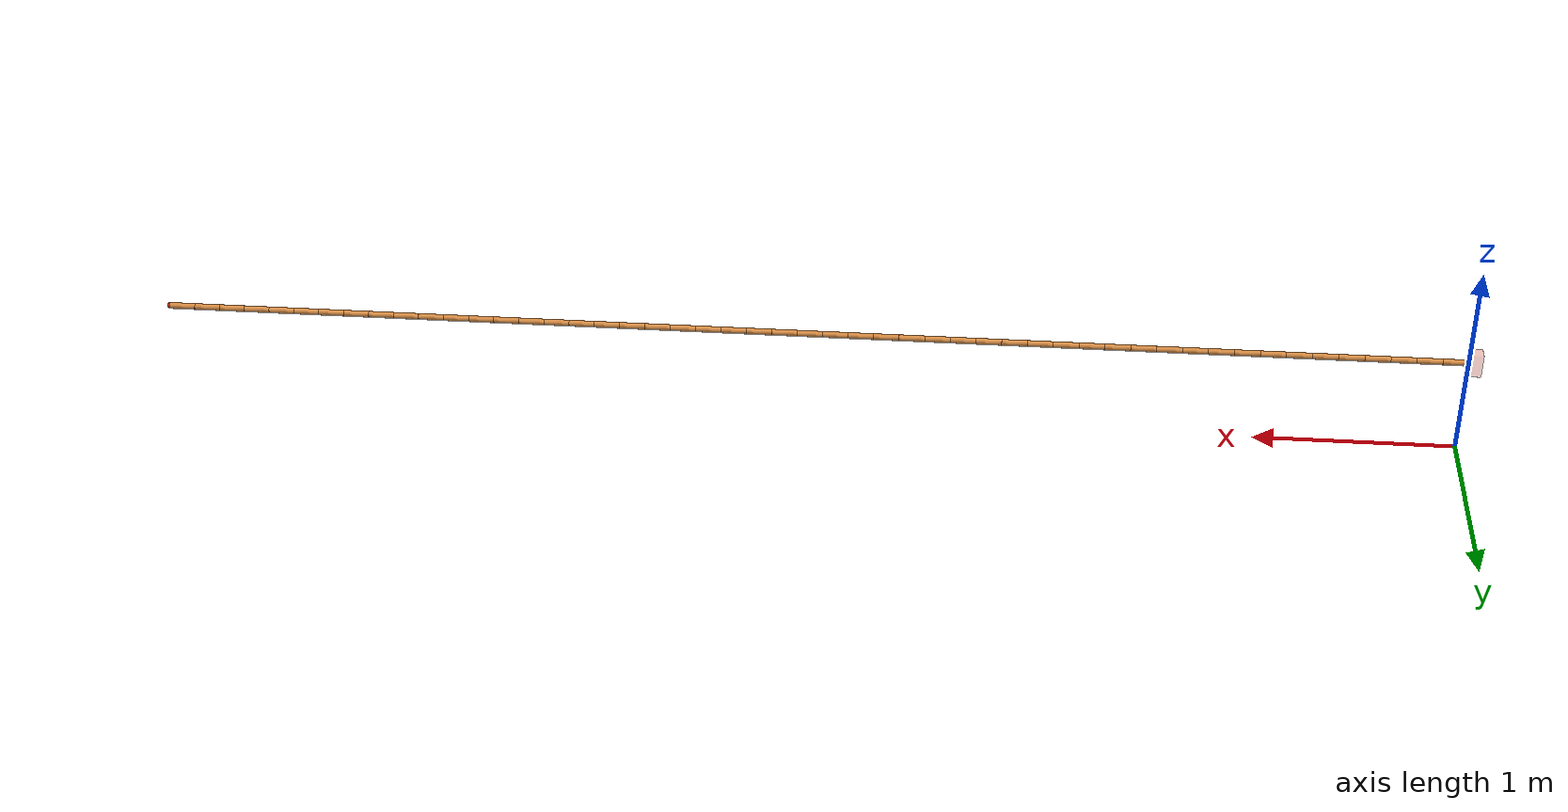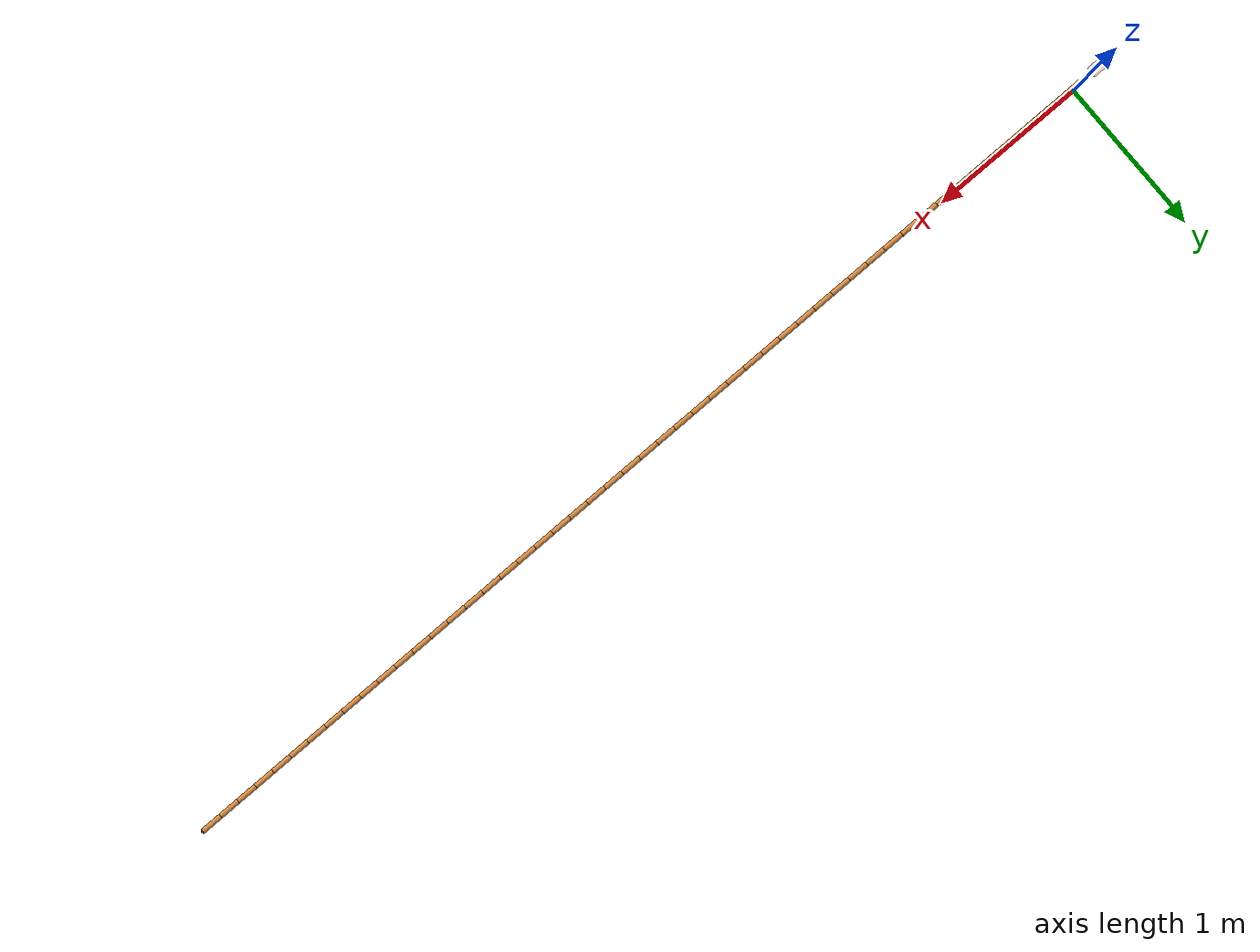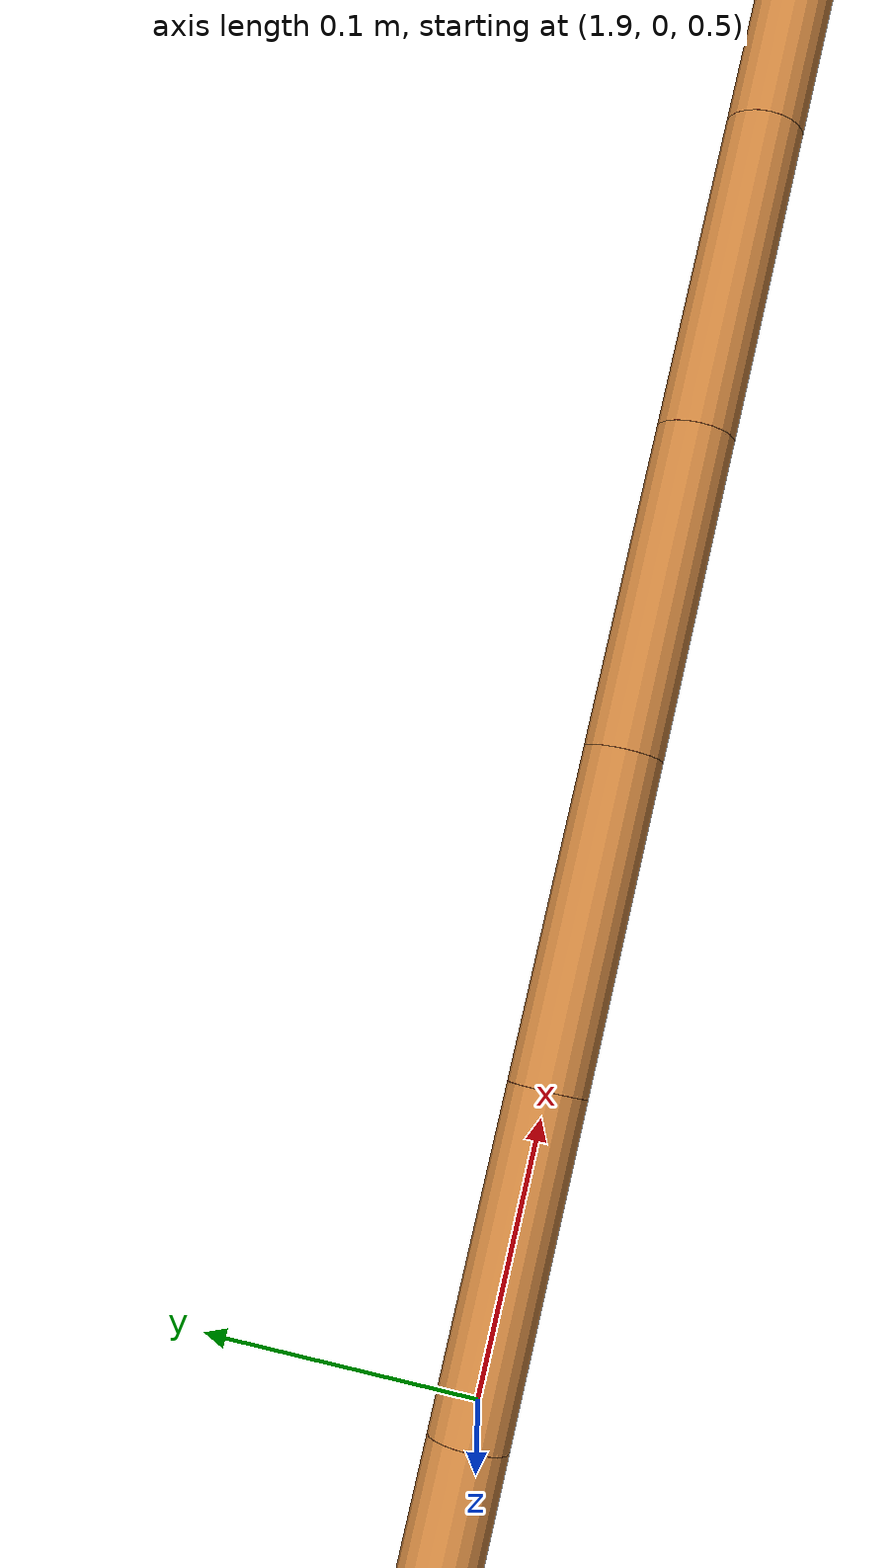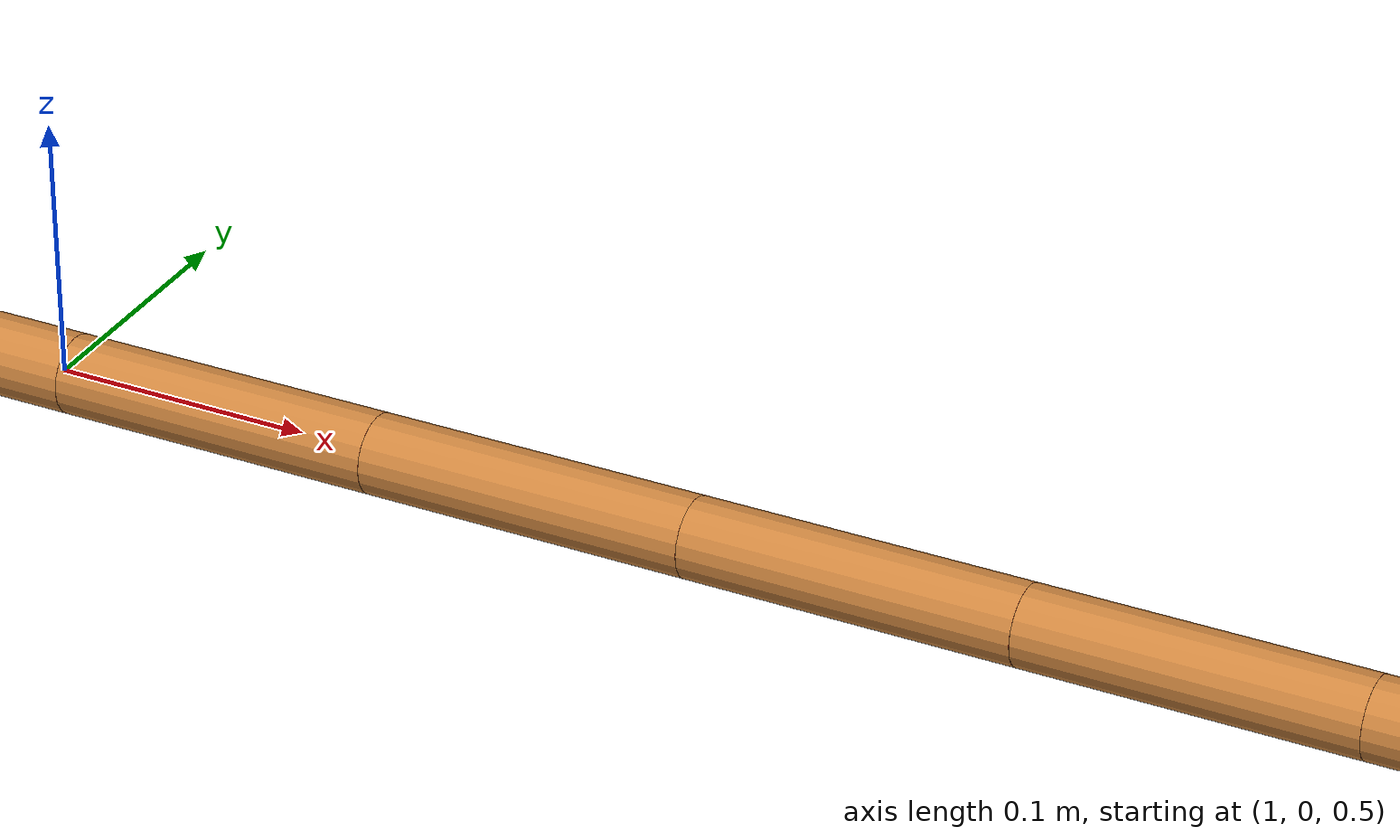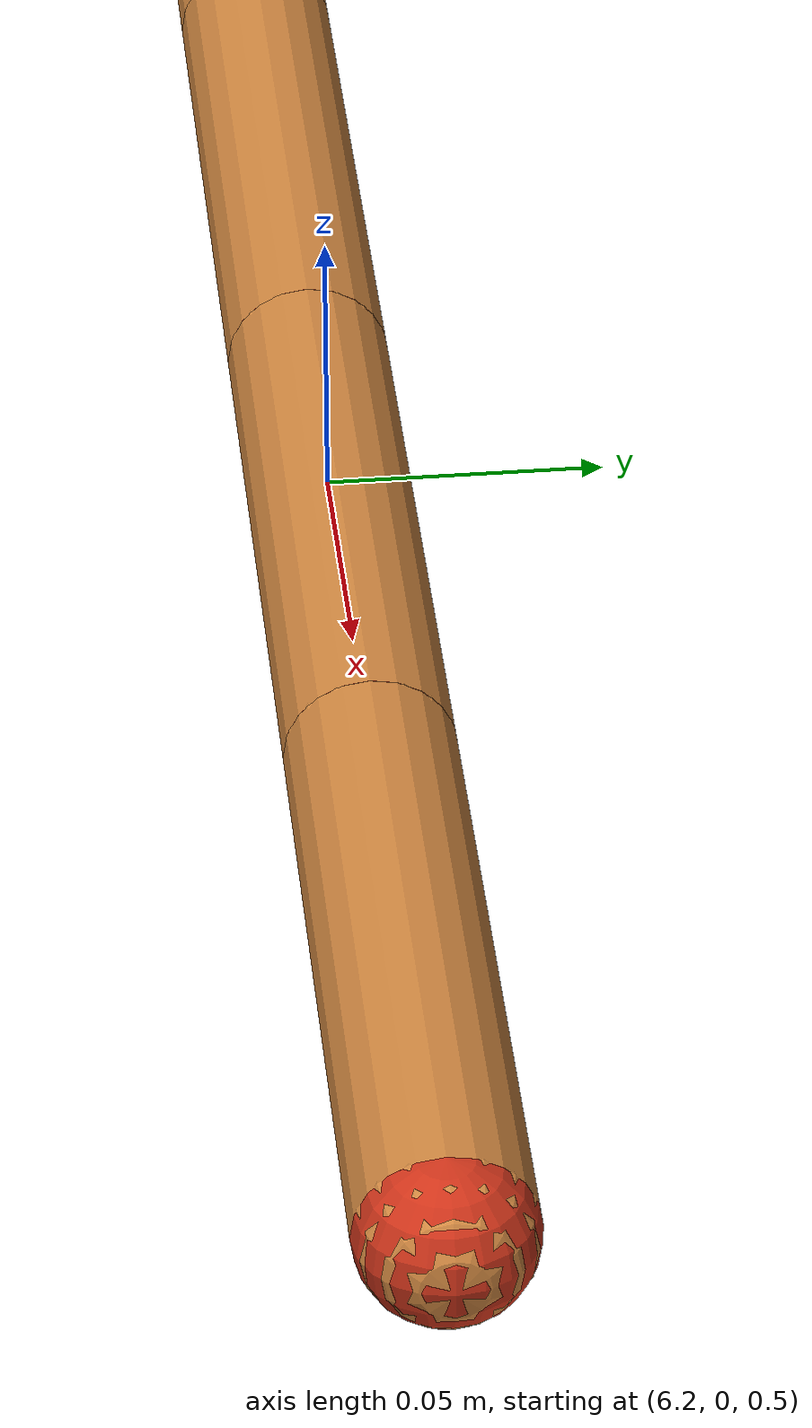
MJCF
<mujoco model="base">
  <statistic extent="2" meansize=".05" />
  <compiler angle="radian" coordinate="local" eulerseq="XYZ" />
  <option impratio="1" timestep="0.0005" solver="Newton" iterations="30" tolerance="1e-10" jacobian="sparse" cone="elliptic" integrator="RK4" />
  <size nconmax="5000" njmax="5000" />

  <asset>
    <texture type="skybox" builtin="gradient" rgb1="1. 1. 0.9" rgb2="0.9 0.9 0.81" width="512" height="512" />
    <texture name="texplane" type="2d" builtin="checker" rgb1=".2 .3 .4" rgb2=".1 0.15 0.2" width="512" height="512" mark="cross" markrgb=".8 .8 .8" />
    <material name="matplane" reflectance="0.3" texture="texplane" texrepeat="1 1" texuniform="true" />
  </asset>

  <visual>
    <rgba haze="0.15 0.25 0.35 1" />
    <quality shadowsize="2048" />
    <map znear="0.001" stiffness="700" shadowscale="0.5" fogstart="10" fogend="15" zfar="40" haze="0.3" />
  </visual>

  <actuator />

  <worldbody>

    <camera mode="fixed" pos="0 -1 1.5" quat="0.866 0.5 0 0" />
    <camera mode="fixed" pos="1. -1.2 0.8" quat="0.687 0.527 0.304 0.397" />
    <camera mode="fixed" pos="-1.8 -1.1 .7" quat="0.73296292  0.56242221 -0.23296292 -0.30360319" />
    <camera mode="fixed" pos="-1 -1.5 .5" quat="0.707 0.707 0 0" />
    <camera mode="fixed" pos="9.7 -1.0 1.1" quat="0.687 0.527 0.304 0.397" />
    <camera mode="fixed" pos="4.5 -8.0 .5" quat="0.707 0.707 0 0" />
    <geom condim="1" material="matplane" name="floor" pos="0 0 -10" size="3 3 .125" type="plane" />
    <light directional="true" diffuse=".4 .4 .4" specular="0.1 0.1 0.1" pos="0 0 5.0" dir="0 0 -1" castshadow="false" />
    <light directional="true" diffuse=".6 .6 .6" specular="0.2 0.2 0.2" pos="0 0 4" dir="0 0 -1" />

  <body name="anchor_box" pos="-0.03000000000000025 -3.942657917179662e-16 0.5">
      <geom name="fixedbox1" type="box" mass="1" size="0.0300 0.0300 0.0600" contype="0" conaffinity="0" rgba=".8 .2 .1 0.3" friction="1 0.005 0.0001" />
    </body>
  <body name="stiffrope" pos="6.346017160251383 0.0 0.5" quat="1 0 0 0">
      <site name="ft_rope" pos="0 0 0" size="0.01 0.01 0.01" rgba="1 0 0 1" type="sphere" group="1" />
      <body name="r_joint0_body" pos="0.06283185307179587 0 0" quat="1.0 0.0 0.0 0.0">
        <site name="r_joint0_site" type="sphere" size="0.0001 0.0001 0.0001" />
        <geom name="r_joint0_geom" conaffinity="0" contype="0" type="sphere" size="0.015 0.015 0.015" mass="0.02513274122871835" rgba=".8 .2 .1 1" friction="1 0.005 0.0001" />
      </body>
      <body name="r_link1_body" pos="0.0 0 0" quat="1.0 0.0 0.0 0.0">
        <body name="r_joint1_body" pos="-0.06283185307179587 0 0">
          <site name="r_joint1_site" type="sphere" size="0.0001 0.0001 0.0001" />
          <geom name="r_joint1_geom" conaffinity="0" contype="0" type="sphere" size="0.015 0.015 0.015" mass="0.02513274122871835" rgba=".8 .2 .1 1" friction="1 0.005 0.0001" />
        </body>
        <geom name="r_link1_geom" quat="0.707 0. 0.707 0." type="capsule" size="0.0150 0.0628" mass="0.22619467105846514" rgba="0.803921568627451 0.5215686274509804 0.24705882352941178 1.0" friction="1 0.005 0.0001" solref="0.01 1" contype="1" conaffinity="1" condim="1" />
        <site name="r_link1_site" type="sphere" size="0.0001 0.0001 0.0001" />
      </body>
    </body>
    <body name="r_link2_body" pos="6.220353454107791 0.0 0.5" quat="1.0 0.0 0.0 0.0">
      <freejoint name="freejoint2" />
      <body name="r_joint2_body" pos="-0.06283185307179587 0 0">
        <site name="r_joint2_site" type="sphere" size="0.0001 0.0001 0.0001" />
        <geom name="r_joint2_geom" conaffinity="0" contype="0" type="sphere" size="0.015 0.015 0.015" mass="0.02513274122871835" rgba=".8 .2 .1 1" friction="1 0.005 0.0001" />
      </body>
      <geom name="r_link2_geom" quat="0.707 0. 0.707 0." type="capsule" size="0.0150 0.0628" mass="0.22619467105846514" rgba="0.803921568627451 0.5215686274509804 0.24705882352941178 1.0" friction="1 0.005 0.0001" solref="0.01 1" contype="1" conaffinity="1" condim="1" />
      <site name="r_link2_site" type="sphere" size="0.0001 0.0001 0.0001" />
    </body>
    <body name="r_link3_body" pos="6.094689747964199 0.0 0.5" quat="1.0 0.0 0.0 0.0">
      <freejoint name="freejoint3" />
      <body name="r_joint3_body" pos="-0.06283185307179587 0 0">
        <site name="r_joint3_site" type="sphere" size="0.0001 0.0001 0.0001" />
        <geom name="r_joint3_geom" conaffinity="0" contype="0" type="sphere" size="0.015 0.015 0.015" mass="0.02513274122871835" rgba=".8 .2 .1 1" friction="1 0.005 0.0001" />
      </body>
      <geom name="r_link3_geom" quat="0.707 0. 0.707 0." type="capsule" size="0.0150 0.0628" mass="0.22619467105846514" rgba="0.803921568627451 0.5215686274509804 0.24705882352941178 1.0" friction="1 0.005 0.0001" solref="0.01 1" contype="1" conaffinity="1" condim="1" />
      <site name="r_link3_site" type="sphere" size="0.0001 0.0001 0.0001" />
    </body>
    <body name="r_link4_body" pos="5.969026041820608 0.0 0.5" quat="1.0 0.0 0.0 0.0">
      <freejoint name="freejoint4" />
      <body name="r_joint4_body" pos="-0.06283185307179587 0 0">
        <site name="r_joint4_site" type="sphere" size="0.0001 0.0001 0.0001" />
        <geom name="r_joint4_geom" conaffinity="0" contype="0" type="sphere" size="0.015 0.015 0.015" mass="0.02513274122871835" rgba=".8 .2 .1 1" friction="1 0.005 0.0001" />
      </body>
      <geom name="r_link4_geom" quat="0.707 0. 0.707 0." type="capsule" size="0.0150 0.0628" mass="0.22619467105846514" rgba="0.803921568627451 0.5215686274509804 0.24705882352941178 1.0" friction="1 0.005 0.0001" solref="0.01 1" contype="1" conaffinity="1" condim="1" />
      <site name="r_link4_site" type="sphere" size="0.0001 0.0001 0.0001" />
    </body>
    <body name="r_link5_body" pos="5.843362335677016 0.0 0.5" quat="1.0 0.0 0.0 0.0">
      <freejoint name="freejoint5" />
      <body name="r_joint5_body" pos="-0.06283185307179587 0 0">
        <site name="r_joint5_site" type="sphere" size="0.0001 0.0001 0.0001" />
        <geom name="r_joint5_geom" conaffinity="0" contype="0" type="sphere" size="0.015 0.015 0.015" mass="0.02513274122871835" rgba=".8 .2 .1 1" friction="1 0.005 0.0001" />
      </body>
      <geom name="r_link5_geom" quat="0.707 0. 0.707 0." type="capsule" size="0.0150 0.0628" mass="0.22619467105846514" rgba="0.803921568627451 0.5215686274509804 0.24705882352941178 1.0" friction="1 0.005 0.0001" solref="0.01 1" contype="1" conaffinity="1" condim="1" />
      <site name="r_link5_site" type="sphere" size="0.0001 0.0001 0.0001" />
    </body>
    <body name="r_link6_body" pos="5.717698629533424 0.0 0.5" quat="1.0 0.0 0.0 0.0">
      <freejoint name="freejoint6" />
      <body name="r_joint6_body" pos="-0.06283185307179587 0 0">
        <site name="r_joint6_site" type="sphere" size="0.0001 0.0001 0.0001" />
        <geom name="r_joint6_geom" conaffinity="0" contype="0" type="sphere" size="0.015 0.015 0.015" mass="0.02513274122871835" rgba=".8 .2 .1 1" friction="1 0.005 0.0001" />
      </body>
      <geom name="r_link6_geom" quat="0.707 0. 0.707 0." type="capsule" size="0.0150 0.0628" mass="0.22619467105846514" rgba="0.803921568627451 0.5215686274509804 0.24705882352941178 1.0" friction="1 0.005 0.0001" solref="0.01 1" contype="1" conaffinity="1" condim="1" />
      <site name="r_link6_site" type="sphere" size="0.0001 0.0001 0.0001" />
    </body>
    <body name="r_link7_body" pos="5.592034923389832 0.0 0.5" quat="1.0 0.0 0.0 0.0">
      <freejoint name="freejoint7" />
      <body name="r_joint7_body" pos="-0.06283185307179587 0 0">
        <site name="r_joint7_site" type="sphere" size="0.0001 0.0001 0.0001" />
        <geom name="r_joint7_geom" conaffinity="0" contype="0" type="sphere" size="0.015 0.015 0.015" mass="0.02513274122871835" rgba=".8 .2 .1 1" friction="1 0.005 0.0001" />
      </body>
      <geom name="r_link7_geom" quat="0.707 0. 0.707 0." type="capsule" size="0.0150 0.0628" mass="0.22619467105846514" rgba="0.803921568627451 0.5215686274509804 0.24705882352941178 1.0" friction="1 0.005 0.0001" solref="0.01 1" contype="1" conaffinity="1" condim="1" />
      <site name="r_link7_site" type="sphere" size="0.0001 0.0001 0.0001" />
    </body>
    <body name="r_link8_body" pos="5.46637121724624 0.0 0.5" quat="1.0 0.0 0.0 0.0">
      <freejoint name="freejoint8" />
      <body name="r_joint8_body" pos="-0.06283185307179587 0 0">
        <site name="r_joint8_site" type="sphere" size="0.0001 0.0001 0.0001" />
        <geom name="r_joint8_geom" conaffinity="0" contype="0" type="sphere" size="0.015 0.015 0.015" mass="0.02513274122871835" rgba=".8 .2 .1 1" friction="1 0.005 0.0001" />
      </body>
      <geom name="r_link8_geom" quat="0.707 0. 0.707 0." type="capsule" size="0.0150 0.0628" mass="0.22619467105846514" rgba="0.803921568627451 0.5215686274509804 0.24705882352941178 1.0" friction="1 0.005 0.0001" solref="0.01 1" contype="1" conaffinity="1" condim="1" />
      <site name="r_link8_site" type="sphere" size="0.0001 0.0001 0.0001" />
    </body>
    <body name="r_link9_body" pos="5.340707511102648 0.0 0.5" quat="1.0 0.0 0.0 0.0">
      <freejoint name="freejoint9" />
      <body name="r_joint9_body" pos="-0.06283185307179587 0 0">
        <site name="r_joint9_site" type="sphere" size="0.0001 0.0001 0.0001" />
        <geom name="r_joint9_geom" conaffinity="0" contype="0" type="sphere" size="0.015 0.015 0.015" mass="0.02513274122871835" rgba=".8 .2 .1 1" friction="1 0.005 0.0001" />
      </body>
      <geom name="r_link9_geom" quat="0.707 0. 0.707 0." type="capsule" size="0.0150 0.0628" mass="0.22619467105846514" rgba="0.803921568627451 0.5215686274509804 0.24705882352941178 1.0" friction="1 0.005 0.0001" solref="0.01 1" contype="1" conaffinity="1" condim="1" />
      <site name="r_link9_site" type="sphere" size="0.0001 0.0001 0.0001" />
    </body>
    <body name="r_link10_body" pos="5.215043804959057 0.0 0.5" quat="1.0 0.0 0.0 0.0">
      <freejoint name="freejoint10" />
      <body name="r_joint10_body" pos="-0.06283185307179587 0 0">
        <site name="r_joint10_site" type="sphere" size="0.0001 0.0001 0.0001" />
        <geom name="r_joint10_geom" conaffinity="0" contype="0" type="sphere" size="0.015 0.015 0.015" mass="0.02513274122871835" rgba=".8 .2 .1 1" friction="1 0.005 0.0001" />
      </body>
      <geom name="r_link10_geom" quat="0.707 0. 0.707 0." type="capsule" size="0.0150 0.0628" mass="0.22619467105846514" rgba="0.803921568627451 0.5215686274509804 0.24705882352941178 1.0" friction="1 0.005 0.0001" solref="0.01 1" contype="1" conaffinity="1" condim="1" />
      <site name="r_link10_site" type="sphere" size="0.0001 0.0001 0.0001" />
    </body>
    <body name="r_link11_body" pos="5.089380098815465 0.0 0.5" quat="1.0 0.0 0.0 0.0">
      <freejoint name="freejoint11" />
      <body name="r_joint11_body" pos="-0.06283185307179587 0 0">
        <site name="r_joint11_site" type="sphere" size="0.0001 0.0001 0.0001" />
        <geom name="r_joint11_geom" conaffinity="0" contype="0" type="sphere" size="0.015 0.015 0.015" mass="0.02513274122871835" rgba=".8 .2 .1 1" friction="1 0.005 0.0001" />
      </body>
      <geom name="r_link11_geom" quat="0.707 0. 0.707 0." type="capsule" size="0.0150 0.0628" mass="0.22619467105846514" rgba="0.803921568627451 0.5215686274509804 0.24705882352941178 1.0" friction="1 0.005 0.0001" solref="0.01 1" contype="1" conaffinity="1" condim="1" />
      <site name="r_link11_site" type="sphere" size="0.0001 0.0001 0.0001" />
    </body>
    <body name="r_link12_body" pos="4.9637163926718735 0.0 0.5" quat="1.0 0.0 0.0 0.0">
      <freejoint name="freejoint12" />
      <body name="r_joint12_body" pos="-0.06283185307179587 0 0">
        <site name="r_joint12_site" type="sphere" size="0.0001 0.0001 0.0001" />
        <geom name="r_joint12_geom" conaffinity="0" contype="0" type="sphere" size="0.015 0.015 0.015" mass="0.02513274122871835" rgba=".8 .2 .1 1" friction="1 0.005 0.0001" />
      </body>
      <geom name="r_link12_geom" quat="0.707 0. 0.707 0." type="capsule" size="0.0150 0.0628" mass="0.22619467105846514" rgba="0.803921568627451 0.5215686274509804 0.24705882352941178 1.0" friction="1 0.005 0.0001" solref="0.01 1" contype="1" conaffinity="1" condim="1" />
      <site name="r_link12_site" type="sphere" size="0.0001 0.0001 0.0001" />
    </body>
    <body name="r_link13_body" pos="4.838052686528282 0.0 0.5" quat="1.0 0.0 0.0 0.0">
      <freejoint name="freejoint13" />
      <body name="r_joint13_body" pos="-0.06283185307179587 0 0">
        <site name="r_joint13_site" type="sphere" size="0.0001 0.0001 0.0001" />
        <geom name="r_joint13_geom" conaffinity="0" contype="0" type="sphere" size="0.015 0.015 0.015" mass="0.02513274122871835" rgba=".8 .2 .1 1" friction="1 0.005 0.0001" />
      </body>
      <geom name="r_link13_geom" quat="0.707 0. 0.707 0." type="capsule" size="0.0150 0.0628" mass="0.22619467105846514" rgba="0.803921568627451 0.5215686274509804 0.24705882352941178 1.0" friction="1 0.005 0.0001" solref="0.01 1" contype="1" conaffinity="1" condim="1" />
      <site name="r_link13_site" type="sphere" size="0.0001 0.0001 0.0001" />
    </body>
    <body name="r_link14_body" pos="4.71238898038469 0.0 0.5" quat="1.0 0.0 0.0 0.0">
      <freejoint name="freejoint14" />
      <body name="r_joint14_body" pos="-0.06283185307179587 0 0">
        <site name="r_joint14_site" type="sphere" size="0.0001 0.0001 0.0001" />
        <geom name="r_joint14_geom" conaffinity="0" contype="0" type="sphere" size="0.015 0.015 0.015" mass="0.02513274122871835" rgba=".8 .2 .1 1" friction="1 0.005 0.0001" />
      </body>
      <geom name="r_link14_geom" quat="0.707 0. 0.707 0." type="capsule" size="0.0150 0.0628" mass="0.22619467105846514" rgba="0.803921568627451 0.5215686274509804 0.24705882352941178 1.0" friction="1 0.005 0.0001" solref="0.01 1" contype="1" conaffinity="1" condim="1" />
      <site name="r_link14_site" type="sphere" size="0.0001 0.0001 0.0001" />
    </body>
    <body name="r_link15_body" pos="4.586725274241099 0.0 0.5" quat="1.0 0.0 0.0 0.0">
      <freejoint name="freejoint15" />
      <body name="r_joint15_body" pos="-0.06283185307179587 0 0">
        <site name="r_joint15_site" type="sphere" size="0.0001 0.0001 0.0001" />
        <geom name="r_joint15_geom" conaffinity="0" contype="0" type="sphere" size="0.015 0.015 0.015" mass="0.02513274122871835" rgba=".8 .2 .1 1" friction="1 0.005 0.0001" />
      </body>
      <geom name="r_link15_geom" quat="0.707 0. 0.707 0." type="capsule" size="0.0150 0.0628" mass="0.22619467105846514" rgba="0.803921568627451 0.5215686274509804 0.24705882352941178 1.0" friction="1 0.005 0.0001" solref="0.01 1" contype="1" conaffinity="1" condim="1" />
      <site name="r_link15_site" type="sphere" size="0.0001 0.0001 0.0001" />
    </body>
    <body name="r_link16_body" pos="4.461061568097507 0.0 0.5" quat="1.0 0.0 0.0 0.0">
      <freejoint name="freejoint16" />
      <body name="r_joint16_body" pos="-0.06283185307179587 0 0">
        <site name="r_joint16_site" type="sphere" size="0.0001 0.0001 0.0001" />
        <geom name="r_joint16_geom" conaffinity="0" contype="0" type="sphere" size="0.015 0.015 0.015" mass="0.02513274122871835" rgba=".8 .2 .1 1" friction="1 0.005 0.0001" />
      </body>
      <geom name="r_link16_geom" quat="0.707 0. 0.707 0." type="capsule" size="0.0150 0.0628" mass="0.22619467105846514" rgba="0.803921568627451 0.5215686274509804 0.24705882352941178 1.0" friction="1 0.005 0.0001" solref="0.01 1" contype="1" conaffinity="1" condim="1" />
      <site name="r_link16_site" type="sphere" size="0.0001 0.0001 0.0001" />
    </body>
    <body name="r_link17_body" pos="4.335397861953915 0.0 0.5" quat="1.0 0.0 0.0 0.0">
      <freejoint name="freejoint17" />
      <body name="r_joint17_body" pos="-0.06283185307179587 0 0">
        <site name="r_joint17_site" type="sphere" size="0.0001 0.0001 0.0001" />
        <geom name="r_joint17_geom" conaffinity="0" contype="0" type="sphere" size="0.015 0.015 0.015" mass="0.02513274122871835" rgba=".8 .2 .1 1" friction="1 0.005 0.0001" />
      </body>
      <geom name="r_link17_geom" quat="0.707 0. 0.707 0." type="capsule" size="0.0150 0.0628" mass="0.22619467105846514" rgba="0.803921568627451 0.5215686274509804 0.24705882352941178 1.0" friction="1 0.005 0.0001" solref="0.01 1" contype="1" conaffinity="1" condim="1" />
      <site name="r_link17_site" type="sphere" size="0.0001 0.0001 0.0001" />
    </body>
    <body name="r_link18_body" pos="4.209734155810323 0.0 0.5" quat="1.0 0.0 0.0 0.0">
      <freejoint name="freejoint18" />
      <body name="r_joint18_body" pos="-0.06283185307179587 0 0">
        <site name="r_joint18_site" type="sphere" size="0.0001 0.0001 0.0001" />
        <geom name="r_joint18_geom" conaffinity="0" contype="0" type="sphere" size="0.015 0.015 0.015" mass="0.02513274122871835" rgba=".8 .2 .1 1" friction="1 0.005 0.0001" />
      </body>
      <geom name="r_link18_geom" quat="0.707 0. 0.707 0." type="capsule" size="0.0150 0.0628" mass="0.22619467105846514" rgba="0.803921568627451 0.5215686274509804 0.24705882352941178 1.0" friction="1 0.005 0.0001" solref="0.01 1" contype="1" conaffinity="1" condim="1" />
      <site name="r_link18_site" type="sphere" size="0.0001 0.0001 0.0001" />
    </body>
    <body name="r_link19_body" pos="4.084070449666731 0.0 0.5" quat="1.0 0.0 0.0 0.0">
      <freejoint name="freejoint19" />
      <body name="r_joint19_body" pos="-0.06283185307179587 0 0">
        <site name="r_joint19_site" type="sphere" size="0.0001 0.0001 0.0001" />
        <geom name="r_joint19_geom" conaffinity="0" contype="0" type="sphere" size="0.015 0.015 0.015" mass="0.02513274122871835" rgba=".8 .2 .1 1" friction="1 0.005 0.0001" />
      </body>
      <geom name="r_link19_geom" quat="0.707 0. 0.707 0." type="capsule" size="0.0150 0.0628" mass="0.22619467105846514" rgba="0.803921568627451 0.5215686274509804 0.24705882352941178 1.0" friction="1 0.005 0.0001" solref="0.01 1" contype="1" conaffinity="1" condim="1" />
      <site name="r_link19_site" type="sphere" size="0.0001 0.0001 0.0001" />
    </body>
    <body name="r_link20_body" pos="3.9584067435231396 0.0 0.5" quat="1.0 0.0 0.0 0.0">
      <freejoint name="freejoint20" />
      <body name="r_joint20_body" pos="-0.06283185307179587 0 0">
        <site name="r_joint20_site" type="sphere" size="0.0001 0.0001 0.0001" />
        <geom name="r_joint20_geom" conaffinity="0" contype="0" type="sphere" size="0.015 0.015 0.015" mass="0.02513274122871835" rgba=".8 .2 .1 1" friction="1 0.005 0.0001" />
      </body>
      <geom name="r_link20_geom" quat="0.707 0. 0.707 0." type="capsule" size="0.0150 0.0628" mass="0.22619467105846514" rgba="0.803921568627451 0.5215686274509804 0.24705882352941178 1.0" friction="1 0.005 0.0001" solref="0.01 1" contype="1" conaffinity="1" condim="1" />
      <site name="r_link20_site" type="sphere" size="0.0001 0.0001 0.0001" />
    </body>
    <body name="r_link21_body" pos="3.832743037379548 0.0 0.5" quat="1.0 0.0 0.0 0.0">
      <freejoint name="freejoint21" />
      <body name="r_joint21_body" pos="-0.06283185307179587 0 0">
        <site name="r_joint21_site" type="sphere" size="0.0001 0.0001 0.0001" />
        <geom name="r_joint21_geom" conaffinity="0" contype="0" type="sphere" size="0.015 0.015 0.015" mass="0.02513274122871835" rgba=".8 .2 .1 1" friction="1 0.005 0.0001" />
      </body>
      <geom name="r_link21_geom" quat="0.707 0. 0.707 0." type="capsule" size="0.0150 0.0628" mass="0.22619467105846514" rgba="0.803921568627451 0.5215686274509804 0.24705882352941178 1.0" friction="1 0.005 0.0001" solref="0.01 1" contype="1" conaffinity="1" condim="1" />
      <site name="r_link21_site" type="sphere" size="0.0001 0.0001 0.0001" />
    </body>
    <body name="r_link22_body" pos="3.7070793312359562 0.0 0.5" quat="1.0 0.0 0.0 0.0">
      <freejoint name="freejoint22" />
      <body name="r_joint22_body" pos="-0.06283185307179587 0 0">
        <site name="r_joint22_site" type="sphere" size="0.0001 0.0001 0.0001" />
        <geom name="r_joint22_geom" conaffinity="0" contype="0" type="sphere" size="0.015 0.015 0.015" mass="0.02513274122871835" rgba=".8 .2 .1 1" friction="1 0.005 0.0001" />
      </body>
      <geom name="r_link22_geom" quat="0.707 0. 0.707 0." type="capsule" size="0.0150 0.0628" mass="0.22619467105846514" rgba="0.803921568627451 0.5215686274509804 0.24705882352941178 1.0" friction="1 0.005 0.0001" solref="0.01 1" contype="1" conaffinity="1" condim="1" />
      <site name="r_link22_site" type="sphere" size="0.0001 0.0001 0.0001" />
    </body>
    <body name="r_link23_body" pos="3.5814156250923643 0.0 0.5" quat="1.0 0.0 0.0 0.0">
      <freejoint name="freejoint23" />
      <body name="r_joint23_body" pos="-0.06283185307179587 0 0">
        <site name="r_joint23_site" type="sphere" size="0.0001 0.0001 0.0001" />
        <geom name="r_joint23_geom" conaffinity="0" contype="0" type="sphere" size="0.015 0.015 0.015" mass="0.02513274122871835" rgba=".8 .2 .1 1" friction="1 0.005 0.0001" />
      </body>
      <geom name="r_link23_geom" quat="0.707 0. 0.707 0." type="capsule" size="0.0150 0.0628" mass="0.22619467105846514" rgba="0.803921568627451 0.5215686274509804 0.24705882352941178 1.0" friction="1 0.005 0.0001" solref="0.01 1" contype="1" conaffinity="1" condim="1" />
      <site name="r_link23_site" type="sphere" size="0.0001 0.0001 0.0001" />
    </body>
    <body name="r_link24_body" pos="3.455751918948773 0.0 0.5" quat="1.0 0.0 0.0 0.0">
      <freejoint name="freejoint24" />
      <body name="r_joint24_body" pos="-0.06283185307179587 0 0">
        <site name="r_joint24_site" type="sphere" size="0.0001 0.0001 0.0001" />
        <geom name="r_joint24_geom" conaffinity="0" contype="0" type="sphere" size="0.015 0.015 0.015" mass="0.02513274122871835" rgba=".8 .2 .1 1" friction="1 0.005 0.0001" />
      </body>
      <geom name="r_link24_geom" quat="0.707 0. 0.707 0." type="capsule" size="0.0150 0.0628" mass="0.22619467105846514" rgba="0.803921568627451 0.5215686274509804 0.24705882352941178 1.0" friction="1 0.005 0.0001" solref="0.01 1" contype="1" conaffinity="1" condim="1" />
      <site name="r_link24_site" type="sphere" size="0.0001 0.0001 0.0001" />
    </body>
    <body name="r_link25_body" pos="3.330088212805181 0.0 0.5" quat="1.0 0.0 0.0 0.0">
      <freejoint name="freejoint25" />
      <body name="r_joint25_body" pos="-0.06283185307179587 0 0">
        <site name="r_joint25_site" type="sphere" size="0.0001 0.0001 0.0001" />
        <geom name="r_joint25_geom" conaffinity="0" contype="0" type="sphere" size="0.015 0.015 0.015" mass="0.02513274122871835" rgba=".8 .2 .1 1" friction="1 0.005 0.0001" />
      </body>
      <geom name="r_link25_geom" quat="0.707 0. 0.707 0." type="capsule" size="0.0150 0.0628" mass="0.22619467105846514" rgba="0.803921568627451 0.5215686274509804 0.24705882352941178 1.0" friction="1 0.005 0.0001" solref="0.01 1" contype="1" conaffinity="1" condim="1" />
      <site name="r_link25_site" type="sphere" size="0.0001 0.0001 0.0001" />
    </body>
    <body name="r_link26_body" pos="3.204424506661589 0.0 0.5" quat="1.0 0.0 0.0 0.0">
      <freejoint name="freejoint26" />
      <body name="r_joint26_body" pos="-0.06283185307179587 0 0">
        <site name="r_joint26_site" type="sphere" size="0.0001 0.0001 0.0001" />
        <geom name="r_joint26_geom" conaffinity="0" contype="0" type="sphere" size="0.015 0.015 0.015" mass="0.02513274122871835" rgba=".8 .2 .1 1" friction="1 0.005 0.0001" />
      </body>
      <geom name="r_link26_geom" quat="0.707 0. 0.707 0." type="capsule" size="0.0150 0.0628" mass="0.22619467105846514" rgba="0.803921568627451 0.5215686274509804 0.24705882352941178 1.0" friction="1 0.005 0.0001" solref="0.01 1" contype="1" conaffinity="1" condim="1" />
      <site name="r_link26_site" type="sphere" size="0.0001 0.0001 0.0001" />
    </body>
    <body name="r_link27_body" pos="3.0787608005179976 0.0 0.5" quat="1.0 0.0 0.0 0.0">
      <freejoint name="freejoint27" />
      <body name="r_joint27_body" pos="-0.06283185307179587 0 0">
        <site name="r_joint27_site" type="sphere" size="0.0001 0.0001 0.0001" />
        <geom name="r_joint27_geom" conaffinity="0" contype="0" type="sphere" size="0.015 0.015 0.015" mass="0.02513274122871835" rgba=".8 .2 .1 1" friction="1 0.005 0.0001" />
      </body>
      <geom name="r_link27_geom" quat="0.707 0. 0.707 0." type="capsule" size="0.0150 0.0628" mass="0.22619467105846514" rgba="0.803921568627451 0.5215686274509804 0.24705882352941178 1.0" friction="1 0.005 0.0001" solref="0.01 1" contype="1" conaffinity="1" condim="1" />
      <site name="r_link27_site" type="sphere" size="0.0001 0.0001 0.0001" />
    </body>
    <body name="r_link28_body" pos="2.9530970943744057 0.0 0.5" quat="1.0 0.0 0.0 0.0">
      <freejoint name="freejoint28" />
      <body name="r_joint28_body" pos="-0.06283185307179587 0 0">
        <site name="r_joint28_site" type="sphere" size="0.0001 0.0001 0.0001" />
        <geom name="r_joint28_geom" conaffinity="0" contype="0" type="sphere" size="0.015 0.015 0.015" mass="0.02513274122871835" rgba=".8 .2 .1 1" friction="1 0.005 0.0001" />
      </body>
      <geom name="r_link28_geom" quat="0.707 0. 0.707 0." type="capsule" size="0.0150 0.0628" mass="0.22619467105846514" rgba="0.803921568627451 0.5215686274509804 0.24705882352941178 1.0" friction="1 0.005 0.0001" solref="0.01 1" contype="1" conaffinity="1" condim="1" />
      <site name="r_link28_site" type="sphere" size="0.0001 0.0001 0.0001" />
    </body>
    <body name="r_link29_body" pos="2.827433388230814 0.0 0.5" quat="1.0 0.0 0.0 0.0">
      <freejoint name="freejoint29" />
      <body name="r_joint29_body" pos="-0.06283185307179587 0 0">
        <site name="r_joint29_site" type="sphere" size="0.0001 0.0001 0.0001" />
        <geom name="r_joint29_geom" conaffinity="0" contype="0" type="sphere" size="0.015 0.015 0.015" mass="0.02513274122871835" rgba=".8 .2 .1 1" friction="1 0.005 0.0001" />
      </body>
      <geom name="r_link29_geom" quat="0.707 0. 0.707 0." type="capsule" size="0.0150 0.0628" mass="0.22619467105846514" rgba="0.803921568627451 0.5215686274509804 0.24705882352941178 1.0" friction="1 0.005 0.0001" solref="0.01 1" contype="1" conaffinity="1" condim="1" />
      <site name="r_link29_site" type="sphere" size="0.0001 0.0001 0.0001" />
    </body>
    <body name="r_link30_body" pos="2.7017696820872223 0.0 0.5" quat="1.0 0.0 0.0 0.0">
      <freejoint name="freejoint30" />
      <body name="r_joint30_body" pos="-0.06283185307179587 0 0">
        <site name="r_joint30_site" type="sphere" size="0.0001 0.0001 0.0001" />
        <geom name="r_joint30_geom" conaffinity="0" contype="0" type="sphere" size="0.015 0.015 0.015" mass="0.02513274122871835" rgba=".8 .2 .1 1" friction="1 0.005 0.0001" />
      </body>
      <geom name="r_link30_geom" quat="0.707 0. 0.707 0." type="capsule" size="0.0150 0.0628" mass="0.22619467105846514" rgba="0.803921568627451 0.5215686274509804 0.24705882352941178 1.0" friction="1 0.005 0.0001" solref="0.01 1" contype="1" conaffinity="1" condim="1" />
      <site name="r_link30_site" type="sphere" size="0.0001 0.0001 0.0001" />
    </body>
    <body name="r_link31_body" pos="2.5761059759436304 0.0 0.5" quat="1.0 0.0 0.0 0.0">
      <freejoint name="freejoint31" />
      <body name="r_joint31_body" pos="-0.06283185307179587 0 0">
        <site name="r_joint31_site" type="sphere" size="0.0001 0.0001 0.0001" />
        <geom name="r_joint31_geom" conaffinity="0" contype="0" type="sphere" size="0.015 0.015 0.015" mass="0.02513274122871835" rgba=".8 .2 .1 1" friction="1 0.005 0.0001" />
      </body>
      <geom name="r_link31_geom" quat="0.707 0. 0.707 0." type="capsule" size="0.0150 0.0628" mass="0.22619467105846514" rgba="0.803921568627451 0.5215686274509804 0.24705882352941178 1.0" friction="1 0.005 0.0001" solref="0.01 1" contype="1" conaffinity="1" condim="1" />
      <site name="r_link31_site" type="sphere" size="0.0001 0.0001 0.0001" />
    </body>
    <body name="r_link32_body" pos="2.450442269800039 0.0 0.5" quat="1.0 0.0 0.0 0.0">
      <freejoint name="freejoint32" />
      <body name="r_joint32_body" pos="-0.06283185307179587 0 0">
        <site name="r_joint32_site" type="sphere" size="0.0001 0.0001 0.0001" />
        <geom name="r_joint32_geom" conaffinity="0" contype="0" type="sphere" size="0.015 0.015 0.015" mass="0.02513274122871835" rgba=".8 .2 .1 1" friction="1 0.005 0.0001" />
      </body>
      <geom name="r_link32_geom" quat="0.707 0. 0.707 0." type="capsule" size="0.0150 0.0628" mass="0.22619467105846514" rgba="0.803921568627451 0.5215686274509804 0.24705882352941178 1.0" friction="1 0.005 0.0001" solref="0.01 1" contype="1" conaffinity="1" condim="1" />
      <site name="r_link32_site" type="sphere" size="0.0001 0.0001 0.0001" />
    </body>
    <body name="r_link33_body" pos="2.324778563656447 0.0 0.5" quat="1.0 0.0 0.0 0.0">
      <freejoint name="freejoint33" />
      <body name="r_joint33_body" pos="-0.06283185307179587 0 0">
        <site name="r_joint33_site" type="sphere" size="0.0001 0.0001 0.0001" />
        <geom name="r_joint33_geom" conaffinity="0" contype="0" type="sphere" size="0.015 0.015 0.015" mass="0.02513274122871835" rgba=".8 .2 .1 1" friction="1 0.005 0.0001" />
      </body>
      <geom name="r_link33_geom" quat="0.707 0. 0.707 0." type="capsule" size="0.0150 0.0628" mass="0.22619467105846514" rgba="0.803921568627451 0.5215686274509804 0.24705882352941178 1.0" friction="1 0.005 0.0001" solref="0.01 1" contype="1" conaffinity="1" condim="1" />
      <site name="r_link33_site" type="sphere" size="0.0001 0.0001 0.0001" />
    </body>
    <body name="r_link34_body" pos="2.199114857512855 0.0 0.5" quat="1.0 0.0 0.0 0.0">
      <freejoint name="freejoint34" />
      <body name="r_joint34_body" pos="-0.06283185307179587 0 0">
        <site name="r_joint34_site" type="sphere" size="0.0001 0.0001 0.0001" />
        <geom name="r_joint34_geom" conaffinity="0" contype="0" type="sphere" size="0.015 0.015 0.015" mass="0.02513274122871835" rgba=".8 .2 .1 1" friction="1 0.005 0.0001" />
      </body>
      <geom name="r_link34_geom" quat="0.707 0. 0.707 0." type="capsule" size="0.0150 0.0628" mass="0.22619467105846514" rgba="0.803921568627451 0.5215686274509804 0.24705882352941178 1.0" friction="1 0.005 0.0001" solref="0.01 1" contype="1" conaffinity="1" condim="1" />
      <site name="r_link34_site" type="sphere" size="0.0001 0.0001 0.0001" />
    </body>
    <body name="r_link35_body" pos="2.0734511513692633 0.0 0.5" quat="1.0 0.0 0.0 0.0">
      <freejoint name="freejoint35" />
      <body name="r_joint35_body" pos="-0.06283185307179587 0 0">
        <site name="r_joint35_site" type="sphere" size="0.0001 0.0001 0.0001" />
        <geom name="r_joint35_geom" conaffinity="0" contype="0" type="sphere" size="0.015 0.015 0.015" mass="0.02513274122871835" rgba=".8 .2 .1 1" friction="1 0.005 0.0001" />
      </body>
      <geom name="r_link35_geom" quat="0.707 0. 0.707 0." type="capsule" size="0.0150 0.0628" mass="0.22619467105846514" rgba="0.803921568627451 0.5215686274509804 0.24705882352941178 1.0" friction="1 0.005 0.0001" solref="0.01 1" contype="1" conaffinity="1" condim="1" />
      <site name="r_link35_site" type="sphere" size="0.0001 0.0001 0.0001" />
    </body>
    <body name="r_link36_body" pos="1.9477874452256723 0.0 0.5" quat="1.0 0.0 0.0 0.0">
      <freejoint name="freejoint36" />
      <body name="r_joint36_body" pos="-0.06283185307179587 0 0">
        <site name="r_joint36_site" type="sphere" size="0.0001 0.0001 0.0001" />
        <geom name="r_joint36_geom" conaffinity="0" contype="0" type="sphere" size="0.015 0.015 0.015" mass="0.02513274122871835" rgba=".8 .2 .1 1" friction="1 0.005 0.0001" />
      </body>
      <geom name="r_link36_geom" quat="0.707 0. 0.707 0." type="capsule" size="0.0150 0.0628" mass="0.22619467105846514" rgba="0.803921568627451 0.5215686274509804 0.24705882352941178 1.0" friction="1 0.005 0.0001" solref="0.01 1" contype="1" conaffinity="1" condim="1" />
      <site name="r_link36_site" type="sphere" size="0.0001 0.0001 0.0001" />
    </body>
    <body name="r_link37_body" pos="1.8221237390820804 0.0 0.5" quat="1.0 0.0 0.0 0.0">
      <freejoint name="freejoint37" />
      <body name="r_joint37_body" pos="-0.06283185307179587 0 0">
        <site name="r_joint37_site" type="sphere" size="0.0001 0.0001 0.0001" />
        <geom name="r_joint37_geom" conaffinity="0" contype="0" type="sphere" size="0.015 0.015 0.015" mass="0.02513274122871835" rgba=".8 .2 .1 1" friction="1 0.005 0.0001" />
      </body>
      <geom name="r_link37_geom" quat="0.707 0. 0.707 0." type="capsule" size="0.0150 0.0628" mass="0.22619467105846514" rgba="0.803921568627451 0.5215686274509804 0.24705882352941178 1.0" friction="1 0.005 0.0001" solref="0.01 1" contype="1" conaffinity="1" condim="1" />
      <site name="r_link37_site" type="sphere" size="0.0001 0.0001 0.0001" />
    </body>
    <body name="r_link38_body" pos="1.6964600329384885 0.0 0.5" quat="1.0 0.0 0.0 0.0">
      <freejoint name="freejoint38" />
      <body name="r_joint38_body" pos="-0.06283185307179587 0 0">
        <site name="r_joint38_site" type="sphere" size="0.0001 0.0001 0.0001" />
        <geom name="r_joint38_geom" conaffinity="0" contype="0" type="sphere" size="0.015 0.015 0.015" mass="0.02513274122871835" rgba=".8 .2 .1 1" friction="1 0.005 0.0001" />
      </body>
      <geom name="r_link38_geom" quat="0.707 0. 0.707 0." type="capsule" size="0.0150 0.0628" mass="0.22619467105846514" rgba="0.803921568627451 0.5215686274509804 0.24705882352941178 1.0" friction="1 0.005 0.0001" solref="0.01 1" contype="1" conaffinity="1" condim="1" />
      <site name="r_link38_site" type="sphere" size="0.0001 0.0001 0.0001" />
    </body>
    <body name="r_link39_body" pos="1.5707963267948966 0.0 0.5" quat="1.0 0.0 0.0 0.0">
      <freejoint name="freejoint39" />
      <body name="r_joint39_body" pos="-0.06283185307179587 0 0">
        <site name="r_joint39_site" type="sphere" size="0.0001 0.0001 0.0001" />
        <geom name="r_joint39_geom" conaffinity="0" contype="0" type="sphere" size="0.015 0.015 0.015" mass="0.02513274122871835" rgba=".8 .2 .1 1" friction="1 0.005 0.0001" />
      </body>
      <geom name="r_link39_geom" quat="0.707 0. 0.707 0." type="capsule" size="0.0150 0.0628" mass="0.22619467105846514" rgba="0.803921568627451 0.5215686274509804 0.24705882352941178 1.0" friction="1 0.005 0.0001" solref="0.01 1" contype="1" conaffinity="1" condim="1" />
      <site name="r_link39_site" type="sphere" size="0.0001 0.0001 0.0001" />
    </body>
    <body name="r_link40_body" pos="1.4451326206513047 0.0 0.5" quat="1.0 0.0 0.0 0.0">
      <freejoint name="freejoint40" />
      <body name="r_joint40_body" pos="-0.06283185307179587 0 0">
        <site name="r_joint40_site" type="sphere" size="0.0001 0.0001 0.0001" />
        <geom name="r_joint40_geom" conaffinity="0" contype="0" type="sphere" size="0.015 0.015 0.015" mass="0.02513274122871835" rgba=".8 .2 .1 1" friction="1 0.005 0.0001" />
      </body>
      <geom name="r_link40_geom" quat="0.707 0. 0.707 0." type="capsule" size="0.0150 0.0628" mass="0.22619467105846514" rgba="0.803921568627451 0.5215686274509804 0.24705882352941178 1.0" friction="1 0.005 0.0001" solref="0.01 1" contype="1" conaffinity="1" condim="1" />
      <site name="r_link40_site" type="sphere" size="0.0001 0.0001 0.0001" />
    </body>
    <body name="r_link41_body" pos="1.3194689145077136 0.0 0.5" quat="1.0 0.0 0.0 0.0">
      <freejoint name="freejoint41" />
      <body name="r_joint41_body" pos="-0.06283185307179587 0 0">
        <site name="r_joint41_site" type="sphere" size="0.0001 0.0001 0.0001" />
        <geom name="r_joint41_geom" conaffinity="0" contype="0" type="sphere" size="0.015 0.015 0.015" mass="0.02513274122871835" rgba=".8 .2 .1 1" friction="1 0.005 0.0001" />
      </body>
      <geom name="r_link41_geom" quat="0.707 0. 0.707 0." type="capsule" size="0.0150 0.0628" mass="0.22619467105846514" rgba="0.803921568627451 0.5215686274509804 0.24705882352941178 1.0" friction="1 0.005 0.0001" solref="0.01 1" contype="1" conaffinity="1" condim="1" />
      <site name="r_link41_site" type="sphere" size="0.0001 0.0001 0.0001" />
    </body>
    <body name="r_link42_body" pos="1.1938052083641217 0.0 0.5" quat="1.0 0.0 0.0 0.0">
      <freejoint name="freejoint42" />
      <body name="r_joint42_body" pos="-0.06283185307179587 0 0">
        <site name="r_joint42_site" type="sphere" size="0.0001 0.0001 0.0001" />
        <geom name="r_joint42_geom" conaffinity="0" contype="0" type="sphere" size="0.015 0.015 0.015" mass="0.02513274122871835" rgba=".8 .2 .1 1" friction="1 0.005 0.0001" />
      </body>
      <geom name="r_link42_geom" quat="0.707 0. 0.707 0." type="capsule" size="0.0150 0.0628" mass="0.22619467105846514" rgba="0.803921568627451 0.5215686274509804 0.24705882352941178 1.0" friction="1 0.005 0.0001" solref="0.01 1" contype="1" conaffinity="1" condim="1" />
      <site name="r_link42_site" type="sphere" size="0.0001 0.0001 0.0001" />
    </body>
    <body name="r_link43_body" pos="1.0681415022205298 0.0 0.5" quat="1.0 0.0 0.0 0.0">
      <freejoint name="freejoint43" />
      <body name="r_joint43_body" pos="-0.06283185307179587 0 0">
        <site name="r_joint43_site" type="sphere" size="0.0001 0.0001 0.0001" />
        <geom name="r_joint43_geom" conaffinity="0" contype="0" type="sphere" size="0.015 0.015 0.015" mass="0.02513274122871835" rgba=".8 .2 .1 1" friction="1 0.005 0.0001" />
      </body>
      <geom name="r_link43_geom" quat="0.707 0. 0.707 0." type="capsule" size="0.0150 0.0628" mass="0.22619467105846514" rgba="0.803921568627451 0.5215686274509804 0.24705882352941178 1.0" friction="1 0.005 0.0001" solref="0.01 1" contype="1" conaffinity="1" condim="1" />
      <site name="r_link43_site" type="sphere" size="0.0001 0.0001 0.0001" />
    </body>
    <body name="r_link44_body" pos="0.9424777960769379 0.0 0.5" quat="1.0 0.0 0.0 0.0">
      <freejoint name="freejoint44" />
      <body name="r_joint44_body" pos="-0.06283185307179587 0 0">
        <site name="r_joint44_site" type="sphere" size="0.0001 0.0001 0.0001" />
        <geom name="r_joint44_geom" conaffinity="0" contype="0" type="sphere" size="0.015 0.015 0.015" mass="0.02513274122871835" rgba=".8 .2 .1 1" friction="1 0.005 0.0001" />
      </body>
      <geom name="r_link44_geom" quat="0.707 0. 0.707 0." type="capsule" size="0.0150 0.0628" mass="0.22619467105846514" rgba="0.803921568627451 0.5215686274509804 0.24705882352941178 1.0" friction="1 0.005 0.0001" solref="0.01 1" contype="1" conaffinity="1" condim="1" />
      <site name="r_link44_site" type="sphere" size="0.0001 0.0001 0.0001" />
    </body>
    <body name="r_link45_body" pos="0.816814089933346 0.0 0.5" quat="1.0 0.0 0.0 0.0">
      <freejoint name="freejoint45" />
      <body name="r_joint45_body" pos="-0.06283185307179587 0 0">
        <site name="r_joint45_site" type="sphere" size="0.0001 0.0001 0.0001" />
        <geom name="r_joint45_geom" conaffinity="0" contype="0" type="sphere" size="0.015 0.015 0.015" mass="0.02513274122871835" rgba=".8 .2 .1 1" friction="1 0.005 0.0001" />
      </body>
      <geom name="r_link45_geom" quat="0.707 0. 0.707 0." type="capsule" size="0.0150 0.0628" mass="0.22619467105846514" rgba="0.803921568627451 0.5215686274509804 0.24705882352941178 1.0" friction="1 0.005 0.0001" solref="0.01 1" contype="1" conaffinity="1" condim="1" />
      <site name="r_link45_site" type="sphere" size="0.0001 0.0001 0.0001" />
    </body>
    <body name="r_link46_body" pos="0.6911503837897541 0.0 0.5" quat="1.0 0.0 0.0 0.0">
      <freejoint name="freejoint46" />
      <body name="r_joint46_body" pos="-0.06283185307179587 0 0">
        <site name="r_joint46_site" type="sphere" size="0.0001 0.0001 0.0001" />
        <geom name="r_joint46_geom" conaffinity="0" contype="0" type="sphere" size="0.015 0.015 0.015" mass="0.02513274122871835" rgba=".8 .2 .1 1" friction="1 0.005 0.0001" />
      </body>
      <geom name="r_link46_geom" quat="0.707 0. 0.707 0." type="capsule" size="0.0150 0.0628" mass="0.22619467105846514" rgba="0.803921568627451 0.5215686274509804 0.24705882352941178 1.0" friction="1 0.005 0.0001" solref="0.01 1" contype="1" conaffinity="1" condim="1" />
      <site name="r_link46_site" type="sphere" size="0.0001 0.0001 0.0001" />
    </body>
    <body name="r_link47_body" pos="0.5654866776461631 0.0 0.5" quat="1.0 0.0 0.0 0.0">
      <freejoint name="freejoint47" />
      <body name="r_joint47_body" pos="-0.06283185307179587 0 0">
        <site name="r_joint47_site" type="sphere" size="0.0001 0.0001 0.0001" />
        <geom name="r_joint47_geom" conaffinity="0" contype="0" type="sphere" size="0.015 0.015 0.015" mass="0.02513274122871835" rgba=".8 .2 .1 1" friction="1 0.005 0.0001" />
      </body>
      <geom name="r_link47_geom" quat="0.707 0. 0.707 0." type="capsule" size="0.0150 0.0628" mass="0.22619467105846514" rgba="0.803921568627451 0.5215686274509804 0.24705882352941178 1.0" friction="1 0.005 0.0001" solref="0.01 1" contype="1" conaffinity="1" condim="1" />
      <site name="r_link47_site" type="sphere" size="0.0001 0.0001 0.0001" />
    </body>
    <body name="r_link48_body" pos="0.4398229715025712 0.0 0.5" quat="1.0 0.0 0.0 0.0">
      <freejoint name="freejoint48" />
      <body name="r_joint48_body" pos="-0.06283185307179587 0 0">
        <site name="r_joint48_site" type="sphere" size="0.0001 0.0001 0.0001" />
        <geom name="r_joint48_geom" conaffinity="0" contype="0" type="sphere" size="0.015 0.015 0.015" mass="0.02513274122871835" rgba=".8 .2 .1 1" friction="1 0.005 0.0001" />
      </body>
      <geom name="r_link48_geom" quat="0.707 0. 0.707 0." type="capsule" size="0.0150 0.0628" mass="0.22619467105846514" rgba="0.803921568627451 0.5215686274509804 0.24705882352941178 1.0" friction="1 0.005 0.0001" solref="0.01 1" contype="1" conaffinity="1" condim="1" />
      <site name="r_link48_site" type="sphere" size="0.0001 0.0001 0.0001" />
    </body>
    <body name="r_link49_body" pos="0.3141592653589793 0.0 0.5" quat="1.0 0.0 0.0 0.0">
      <freejoint name="freejoint49" />
      <body name="r_joint49_body" pos="-0.06283185307179587 0 0">
        <site name="r_joint49_site" type="sphere" size="0.0001 0.0001 0.0001" />
        <geom name="r_joint49_geom" conaffinity="0" contype="0" type="sphere" size="0.015 0.015 0.015" mass="0.02513274122871835" rgba=".8 .2 .1 1" friction="1 0.005 0.0001" />
      </body>
      <geom name="r_link49_geom" quat="0.707 0. 0.707 0." type="capsule" size="0.0150 0.0628" mass="0.22619467105846514" rgba="0.803921568627451 0.5215686274509804 0.24705882352941178 1.0" friction="1 0.005 0.0001" solref="0.01 1" contype="1" conaffinity="1" condim="1" />
      <site name="r_link49_site" type="sphere" size="0.0001 0.0001 0.0001" />
    </body>
    <body name="r_link50_body" pos="0.1884955592153874 0.0 0.5" quat="1.0 0.0 0.0 0.0">
      <freejoint name="freejoint50" />
      <body name="r_joint50_body" pos="-0.06283185307179587 0 0">
        <site name="r_joint50_site" type="sphere" size="0.0001 0.0001 0.0001" />
        <geom name="r_joint50_geom" conaffinity="0" contype="0" type="sphere" size="0.015 0.015 0.015" mass="0.02513274122871835" rgba=".8 .2 .1 1" friction="1 0.005 0.0001" />
      </body>
      <geom name="r_link50_geom" quat="0.707 0. 0.707 0." type="capsule" size="0.0150 0.0628" mass="0.22619467105846514" rgba="0.803921568627451 0.5215686274509804 0.24705882352941178 1.0" friction="1 0.005 0.0001" solref="0.01 1" contype="1" conaffinity="1" condim="1" />
      <site name="r_link50_site" type="sphere" size="0.0001 0.0001 0.0001" />
    </body>
    <body name="r_link51_body" pos="0.06283185307179551 0.0 0.5" quat="1.0 0.0 0.0 0.0">
      <freejoint name="freejoint51" />
      <body name="r_joint51_body" pos="-0.06283185307179587 0 0">
        <site name="r_joint51_site" type="sphere" size="0.0001 0.0001 0.0001" />
        <geom name="r_joint51_geom" conaffinity="0" contype="0" type="sphere" size="0.015 0.015 0.015" mass="0.02513274122871835" rgba=".8 .2 .1 1" friction="1 0.005 0.0001" />
      </body>
      <geom name="r_link51_geom" quat="0.707 0. 0.707 0." type="capsule" size="0.0150 0.0628" mass="0.22619467105846514" rgba="0.803921568627451 0.5215686274509804 0.24705882352941178 1.0" friction="1 0.005 0.0001" solref="0.01 1" contype="1" conaffinity="1" condim="1" />
      <site name="r_link51_site" type="sphere" size="0.0001 0.0001 0.0001" />
    </body>
  </worldbody>

  <sensor />

  <equality><weld body1="anchor_box" body2="r_joint51_body" solref="0.004 1" relpose="0.03 0 0 1 0 0 0" />
     <connect body1="r_link1_body" body2="r_link2_body" active="true" solref="0.004 1" anchor="-0.06283185307179587 0 0" />
     <connect body1="r_link2_body" body2="r_link3_body" active="true" solref="0.004 1" anchor="-0.06283185307179587 0 0" />
     <connect body1="r_link3_body" body2="r_link4_body" active="true" solref="0.004 1" anchor="-0.06283185307179587 0 0" />
     <connect body1="r_link4_body" body2="r_link5_body" active="true" solref="0.004 1" anchor="-0.06283185307179587 0 0" />
     <connect body1="r_link5_body" body2="r_link6_body" active="true" solref="0.004 1" anchor="-0.06283185307179587 0 0" />
     <connect body1="r_link6_body" body2="r_link7_body" active="true" solref="0.004 1" anchor="-0.06283185307179587 0 0" />
     <connect body1="r_link7_body" body2="r_link8_body" active="true" solref="0.004 1" anchor="-0.06283185307179587 0 0" />
     <connect body1="r_link8_body" body2="r_link9_body" active="true" solref="0.004 1" anchor="-0.06283185307179587 0 0" />
     <connect body1="r_link9_body" body2="r_link10_body" active="true" solref="0.004 1" anchor="-0.06283185307179587 0 0" />
     <connect body1="r_link10_body" body2="r_link11_body" active="true" solref="0.004 1" anchor="-0.06283185307179587 0 0" />
     <connect body1="r_link11_body" body2="r_link12_body" active="true" solref="0.004 1" anchor="-0.06283185307179587 0 0" />
     <connect body1="r_link12_body" body2="r_link13_body" active="true" solref="0.004 1" anchor="-0.06283185307179587 0 0" />
     <connect body1="r_link13_body" body2="r_link14_body" active="true" solref="0.004 1" anchor="-0.06283185307179587 0 0" />
     <connect body1="r_link14_body" body2="r_link15_body" active="true" solref="0.004 1" anchor="-0.06283185307179587 0 0" />
     <connect body1="r_link15_body" body2="r_link16_body" active="true" solref="0.004 1" anchor="-0.06283185307179587 0 0" />
     <connect body1="r_link16_body" body2="r_link17_body" active="true" solref="0.004 1" anchor="-0.06283185307179587 0 0" />
     <connect body1="r_link17_body" body2="r_link18_body" active="true" solref="0.004 1" anchor="-0.06283185307179587 0 0" />
     <connect body1="r_link18_body" body2="r_link19_body" active="true" solref="0.004 1" anchor="-0.06283185307179587 0 0" />
     <connect body1="r_link19_body" body2="r_link20_body" active="true" solref="0.004 1" anchor="-0.06283185307179587 0 0" />
     <connect body1="r_link20_body" body2="r_link21_body" active="true" solref="0.004 1" anchor="-0.06283185307179587 0 0" />
     <connect body1="r_link21_body" body2="r_link22_body" active="true" solref="0.004 1" anchor="-0.06283185307179587 0 0" />
     <connect body1="r_link22_body" body2="r_link23_body" active="true" solref="0.004 1" anchor="-0.06283185307179587 0 0" />
     <connect body1="r_link23_body" body2="r_link24_body" active="true" solref="0.004 1" anchor="-0.06283185307179587 0 0" />
     <connect body1="r_link24_body" body2="r_link25_body" active="true" solref="0.004 1" anchor="-0.06283185307179587 0 0" />
     <connect body1="r_link25_body" body2="r_link26_body" active="true" solref="0.004 1" anchor="-0.06283185307179587 0 0" />
     <connect body1="r_link26_body" body2="r_link27_body" active="true" solref="0.004 1" anchor="-0.06283185307179587 0 0" />
     <connect body1="r_link27_body" body2="r_link28_body" active="true" solref="0.004 1" anchor="-0.06283185307179587 0 0" />
     <connect body1="r_link28_body" body2="r_link29_body" active="true" solref="0.004 1" anchor="-0.06283185307179587 0 0" />
     <connect body1="r_link29_body" body2="r_link30_body" active="true" solref="0.004 1" anchor="-0.06283185307179587 0 0" />
     <connect body1="r_link30_body" body2="r_link31_body" active="true" solref="0.004 1" anchor="-0.06283185307179587 0 0" />
     <connect body1="r_link31_body" body2="r_link32_body" active="true" solref="0.004 1" anchor="-0.06283185307179587 0 0" />
     <connect body1="r_link32_body" body2="r_link33_body" active="true" solref="0.004 1" anchor="-0.06283185307179587 0 0" />
     <connect body1="r_link33_body" body2="r_link34_body" active="true" solref="0.004 1" anchor="-0.06283185307179587 0 0" />
     <connect body1="r_link34_body" body2="r_link35_body" active="true" solref="0.004 1" anchor="-0.06283185307179587 0 0" />
     <connect body1="r_link35_body" body2="r_link36_body" active="true" solref="0.004 1" anchor="-0.06283185307179587 0 0" />
     <connect body1="r_link36_body" body2="r_link37_body" active="true" solref="0.004 1" anchor="-0.06283185307179587 0 0" />
     <connect body1="r_link37_body" body2="r_link38_body" active="true" solref="0.004 1" anchor="-0.06283185307179587 0 0" />
     <connect body1="r_link38_body" body2="r_link39_body" active="true" solref="0.004 1" anchor="-0.06283185307179587 0 0" />
     <connect body1="r_link39_body" body2="r_link40_body" active="true" solref="0.004 1" anchor="-0.06283185307179587 0 0" />
     <connect body1="r_link40_body" body2="r_link41_body" active="true" solref="0.004 1" anchor="-0.06283185307179587 0 0" />
     <connect body1="r_link41_body" body2="r_link42_body" active="true" solref="0.004 1" anchor="-0.06283185307179587 0 0" />
     <connect body1="r_link42_body" body2="r_link43_body" active="true" solref="0.004 1" anchor="-0.06283185307179587 0 0" />
     <connect body1="r_link43_body" body2="r_link44_body" active="true" solref="0.004 1" anchor="-0.06283185307179587 0 0" />
     <connect body1="r_link44_body" body2="r_link45_body" active="true" solref="0.004 1" anchor="-0.06283185307179587 0 0" />
     <connect body1="r_link45_body" body2="r_link46_body" active="true" solref="0.004 1" anchor="-0.06283185307179587 0 0" />
     <connect body1="r_link46_body" body2="r_link47_body" active="true" solref="0.004 1" anchor="-0.06283185307179587 0 0" />
     <connect body1="r_link47_body" body2="r_link48_body" active="true" solref="0.004 1" anchor="-0.06283185307179587 0 0" />
     <connect body1="r_link48_body" body2="r_link49_body" active="true" solref="0.004 1" anchor="-0.06283185307179587 0 0" />
     <connect body1="r_link49_body" body2="r_link50_body" active="true" solref="0.004 1" anchor="-0.06283185307179587 0 0" />
     <connect body1="r_link50_body" body2="r_link51_body" active="true" solref="0.004 1" anchor="-0.06283185307179587 0 0" />
  </equality>

  <contact><exclude body1="r_link1_body" body2="r_link51_body" />
    <exclude body1="r_link1_body" body2="r_link50_body" />
    <exclude body1="r_link2_body" body2="r_link51_body" />
    <exclude body1="r_link1_body" body2="r_link2_body" />
    <exclude body1="r_link2_body" body2="r_link3_body" />
    <exclude body1="r_link3_body" body2="r_link4_body" />
    <exclude body1="r_link4_body" body2="r_link5_body" />
    <exclude body1="r_link5_body" body2="r_link6_body" />
    <exclude body1="r_link6_body" body2="r_link7_body" />
    <exclude body1="r_link7_body" body2="r_link8_body" />
    <exclude body1="r_link8_body" body2="r_link9_body" />
    <exclude body1="r_link9_body" body2="r_link10_body" />
    <exclude body1="r_link10_body" body2="r_link11_body" />
    <exclude body1="r_link11_body" body2="r_link12_body" />
    <exclude body1="r_link12_body" body2="r_link13_body" />
    <exclude body1="r_link13_body" body2="r_link14_body" />
    <exclude body1="r_link14_body" body2="r_link15_body" />
    <exclude body1="r_link15_body" body2="r_link16_body" />
    <exclude body1="r_link16_body" body2="r_link17_body" />
    <exclude body1="r_link17_body" body2="r_link18_body" />
    <exclude body1="r_link18_body" body2="r_link19_body" />
    <exclude body1="r_link19_body" body2="r_link20_body" />
    <exclude body1="r_link20_body" body2="r_link21_body" />
    <exclude body1="r_link21_body" body2="r_link22_body" />
    <exclude body1="r_link22_body" body2="r_link23_body" />
    <exclude body1="r_link23_body" body2="r_link24_body" />
    <exclude body1="r_link24_body" body2="r_link25_body" />
    <exclude body1="r_link25_body" body2="r_link26_body" />
    <exclude body1="r_link26_body" body2="r_link27_body" />
    <exclude body1="r_link27_body" body2="r_link28_body" />
    <exclude body1="r_link28_body" body2="r_link29_body" />
    <exclude body1="r_link29_body" body2="r_link30_body" />
    <exclude body1="r_link30_body" body2="r_link31_body" />
    <exclude body1="r_link31_body" body2="r_link32_body" />
    <exclude body1="r_link32_body" body2="r_link33_body" />
    <exclude body1="r_link33_body" body2="r_link34_body" />
    <exclude body1="r_link34_body" body2="r_link35_body" />
    <exclude body1="r_link35_body" body2="r_link36_body" />
    <exclude body1="r_link36_body" body2="r_link37_body" />
    <exclude body1="r_link37_body" body2="r_link38_body" />
    <exclude body1="r_link38_body" body2="r_link39_body" />
    <exclude body1="r_link39_body" body2="r_link40_body" />
    <exclude body1="r_link40_body" body2="r_link41_body" />
    <exclude body1="r_link41_body" body2="r_link42_body" />
    <exclude body1="r_link42_body" body2="r_link43_body" />
    <exclude body1="r_link43_body" body2="r_link44_body" />
    <exclude body1="r_link44_body" body2="r_link45_body" />
    <exclude body1="r_link45_body" body2="r_link46_body" />
    <exclude body1="r_link46_body" body2="r_link47_body" />
    <exclude body1="r_link47_body" body2="r_link48_body" />
    <exclude body1="r_link48_body" body2="r_link49_body" />
    <exclude body1="r_link49_body" body2="r_link50_body" />
    <exclude body1="r_link50_body" body2="r_link51_body" />
  </contact>
</mujoco>
